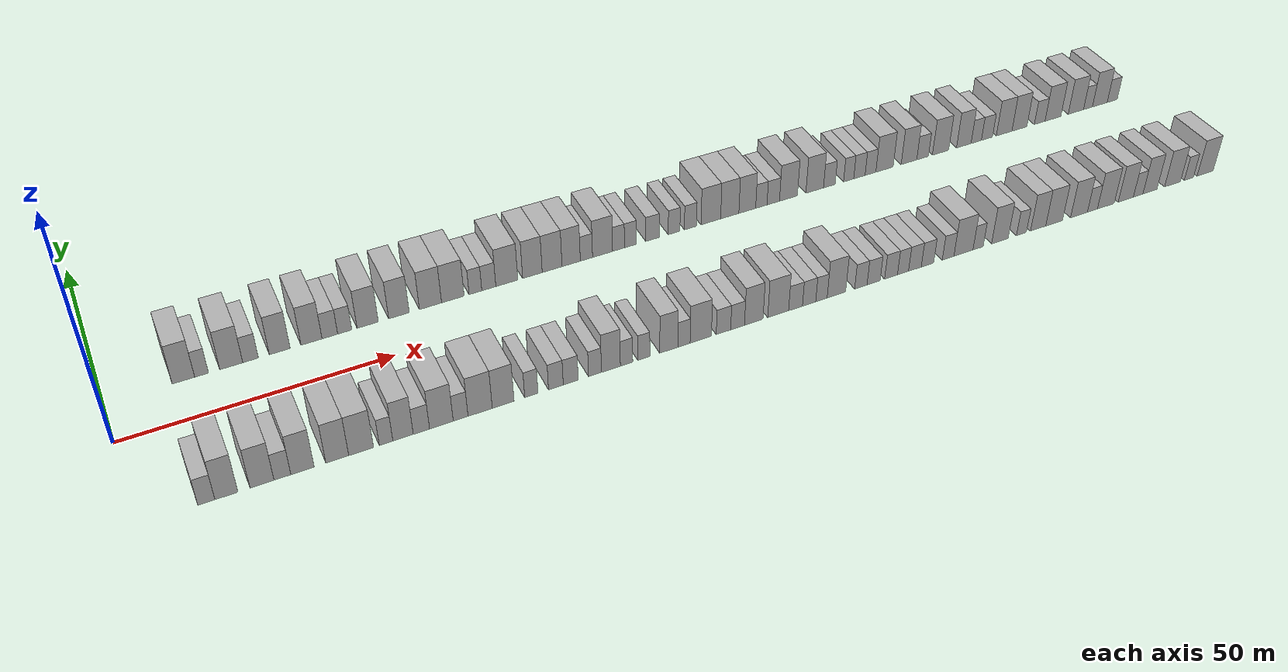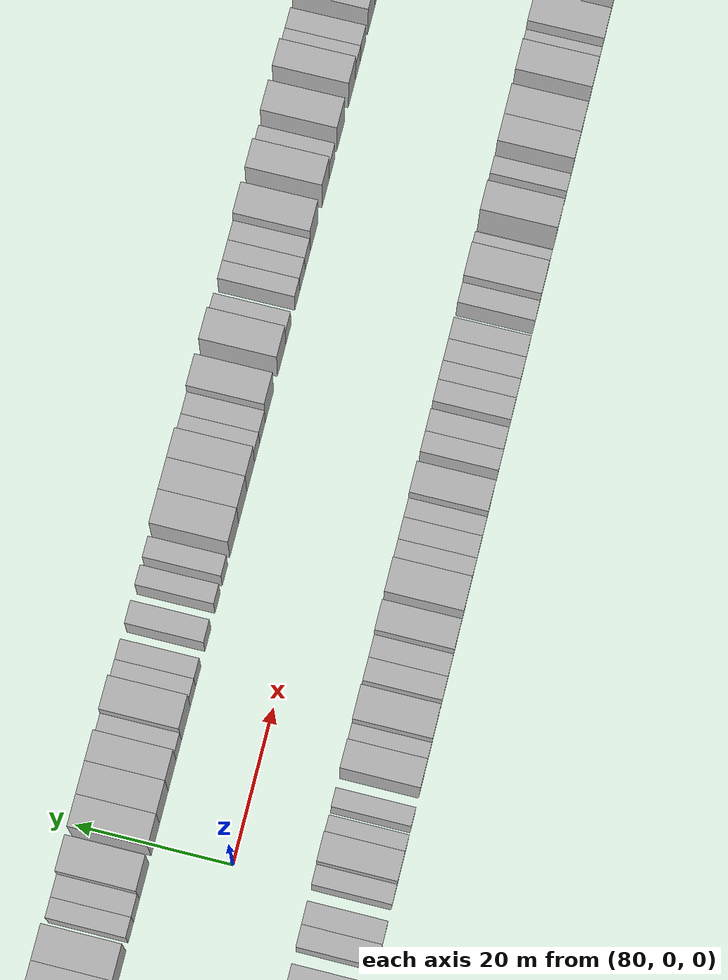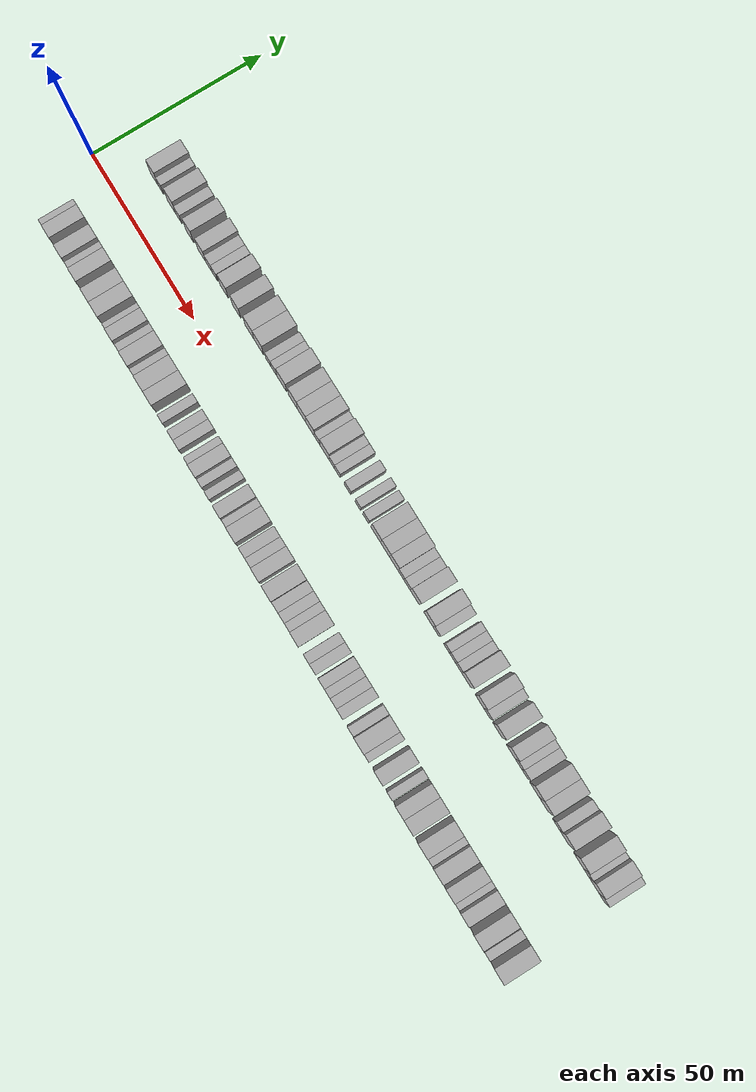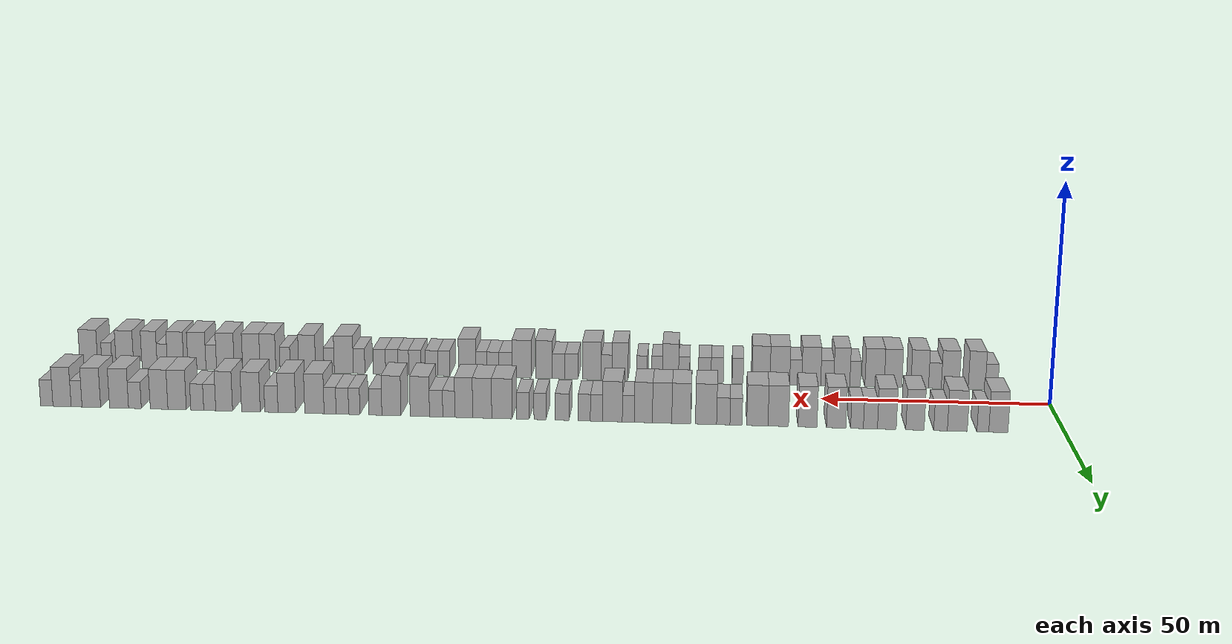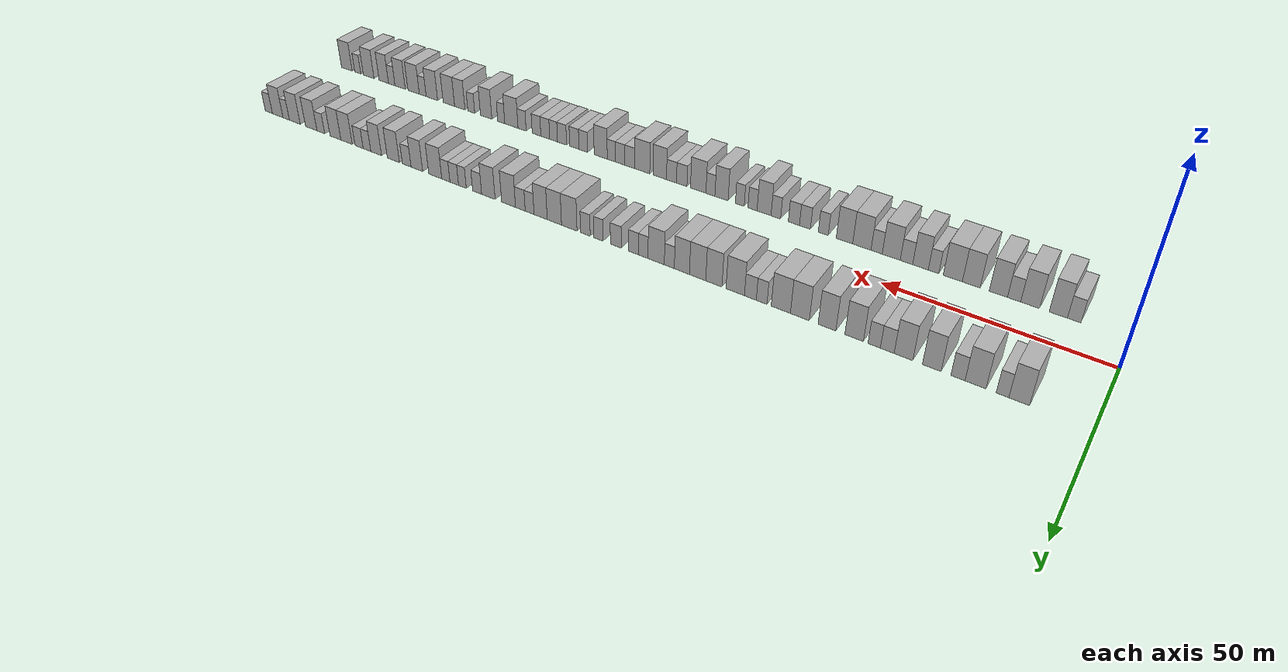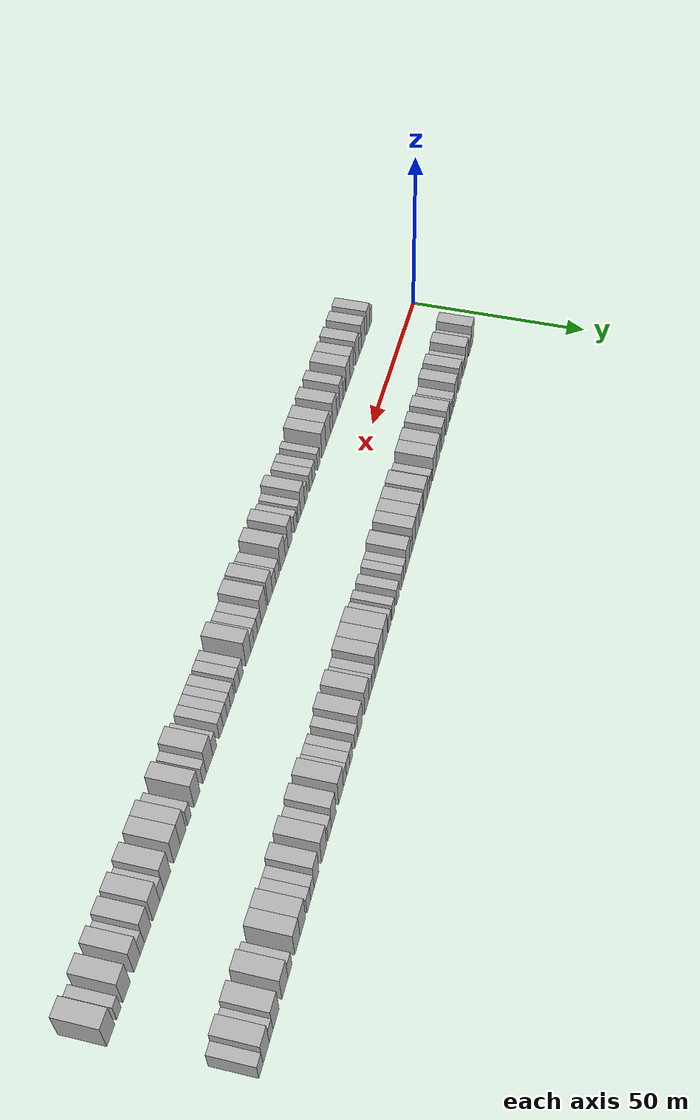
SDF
<sdf version="1.6">
 <world name="default">
  <scene>
   <sky><clouds><speed>12</speed></clouds></sky>
   <ambient>0.4 0.4 0.4 1</ambient>
   <background>0.7 0.7 0.7 1</background>
   <shadows>1</shadows>
  </scene>
  <gravity>0 0 -9.8066</gravity>
  <magnetic_field>6e-06 2.3e-05 -4.2e-05</magnetic_field>
  <physics default="0" name="default_physics" type="ode">
   <ode>
    <solver>
     <type>quick</type>
     <iters>10</iters>
     <sor>1.0</sor>
     <use_dynamic_moi_rescaling>0</use_dynamic_moi_rescaling>
    </solver>
    <constraints>
     <cfm>0</cfm>
     <erp>0.2</erp>
     <contact_max_correcting_vel>100</contact_max_correcting_vel>
     <contact_surface_layer>0.001</contact_surface_layer>
    </constraints>
   </ode>
   <max_step_size>0.004</max_step_size>
   <real_time_factor>1</real_time_factor>
   <real_time_update_rate>250</real_time_update_rate>
  </physics>
  <light name="sun" type="directional">
   <pose>0 0 10 0 0 0</pose>
   <diffuse>0.8 0.8 0.8 1</diffuse>
   <specular>0.2 0.2 0.2 1</specular>
   <attenuation>
    <range>1000</range>
    <constant>0.9</constant>
    <linear>0.01</linear>
    <quadratic>0.001</quadratic>
   </attenuation>
   <direction>-0.5 0.1 -0.9</direction>
  </light>
  <model name="building_1">
   <static>1</static>
   <pose>13.9863 15.0000 0 0.000000 0.000000 1.570796</pose>
   <link name="link">
    <pose>0 0 4.50 0 0 0</pose>
    <collision name="collision"><geometry><box><size>10.0000 3.9726 9.0000</size></box></geometry></collision>
    <visual name="visual">
     <cast_shadows>0</cast_shadows>
     <geometry><box><size>10.0000 3.9726 9.0000</size></box></geometry>
     <material>
      <script>
       <uri>model://HANNAS_wall/materials/scripts</uri>
       <uri>model://HANNAS_wall/materials/textures</uri>
       <name>vrc/HANNAS_wall</name>
      </script>
     </material>
    </visual>
   </link>
  </model>
  <model name="building_2">
   <static>1</static>
   <pose>17.2035 15.0000 0 0.000000 0.000000 1.570796</pose>
   <link name="link">
    <pose>0 0 3.00 0 0 0</pose>
    <collision name="collision"><geometry><box><size>10.0000 2.4617 6.0000</size></box></geometry></collision>
    <visual name="visual">
     <cast_shadows>0</cast_shadows>
     <geometry><box><size>10.0000 2.4617 6.0000</size></box></geometry>
     <material>
      <script>
       <uri>model://HANNAS_wall/materials/scripts</uri>
       <uri>model://HANNAS_wall/materials/textures</uri>
       <name>vrc/HANNAS_wall</name>
      </script>
     </material>
    </visual>
   </link>
  </model>
  <model name="building_3">
   <static>1</static>
   <pose>22.5151 15.0000 0 0.000000 0.000000 1.570796</pose>
   <link name="link">
    <pose>0 0 4.50 0 0 0</pose>
    <collision name="collision"><geometry><box><size>10.0000 4.1615 9.0000</size></box></geometry></collision>
    <visual name="visual">
     <cast_shadows>0</cast_shadows>
     <geometry><box><size>10.0000 4.1615 9.0000</size></box></geometry>
     <material>
      <script>
       <uri>model://HANNAS_wall/materials/scripts</uri>
       <uri>model://HANNAS_wall/materials/textures</uri>
       <name>vrc/HANNAS_wall</name>
      </script>
     </material>
    </visual>
   </link>
  </model>
  <model name="building_4">
   <static>1</static>
   <pose>26.0151 15.0000 0 0.000000 0.000000 1.570796</pose>
   <link name="link">
    <pose>0 0 3.00 0 0 0</pose>
    <collision name="collision"><geometry><box><size>10.0000 2.8385 6.0000</size></box></geometry></collision>
    <visual name="visual">
     <cast_shadows>0</cast_shadows>
     <geometry><box><size>10.0000 2.8385 6.0000</size></box></geometry>
     <material>
      <script>
       <uri>model://HANNAS_wall/materials/scripts</uri>
       <uri>model://HANNAS_wall/materials/textures</uri>
       <name>vrc/HANNAS_wall</name>
      </script>
     </material>
    </visual>
   </link>
  </model>
  <model name="building_5">
   <static>1</static>
   <pose>31.3539 15.0000 0 0.000000 0.000000 1.570796</pose>
   <link name="link">
    <pose>0 0 4.50 0 0 0</pose>
    <collision name="collision"><geometry><box><size>10.0000 3.8392 9.0000</size></box></geometry></collision>
    <visual name="visual">
     <cast_shadows>0</cast_shadows>
     <geometry><box><size>10.0000 3.8392 9.0000</size></box></geometry>
     <material>
      <script>
       <uri>model://HANNAS_wall/materials/scripts</uri>
       <uri>model://HANNAS_wall/materials/textures</uri>
       <name>vrc/HANNAS_wall</name>
      </script>
     </material>
    </visual>
   </link>
  </model>
  <model name="building_6">
   <static>1</static>
   <pose>37.2430 15.0000 0 0.000000 0.000000 1.570796</pose>
   <link name="link">
    <pose>0 0 4.50 0 0 0</pose>
    <collision name="collision"><geometry><box><size>10.0000 3.9389 9.0000</size></box></geometry></collision>
    <visual name="visual">
     <cast_shadows>0</cast_shadows>
     <geometry><box><size>10.0000 3.9389 9.0000</size></box></geometry>
     <material>
      <script>
       <uri>model://HANNAS_wall/materials/scripts</uri>
       <uri>model://HANNAS_wall/materials/textures</uri>
       <name>vrc/HANNAS_wall</name>
      </script>
     </material>
    </visual>
   </link>
  </model>
  <model name="building_7">
   <static>1</static>
   <pose>40.6891 15.0000 0 0.000000 0.000000 1.570796</pose>
   <link name="link">
    <pose>0 0 3.00 0 0 0</pose>
    <collision name="collision"><geometry><box><size>10.0000 2.9532 6.0000</size></box></geometry></collision>
    <visual name="visual">
     <cast_shadows>0</cast_shadows>
     <geometry><box><size>10.0000 2.9532 6.0000</size></box></geometry>
     <material>
      <script>
       <uri>model://HANNAS_wall/materials/scripts</uri>
       <uri>model://HANNAS_wall/materials/textures</uri>
       <name>vrc/HANNAS_wall</name>
      </script>
     </material>
    </visual>
   </link>
  </model>
  <model name="building_8">
   <static>1</static>
   <pose>43.5024 15.0000 0 0.000000 0.000000 1.570796</pose>
   <link name="link">
    <pose>0 0 3.00 0 0 0</pose>
    <collision name="collision"><geometry><box><size>10.0000 2.6734 6.0000</size></box></geometry></collision>
    <visual name="visual">
     <cast_shadows>0</cast_shadows>
     <geometry><box><size>10.0000 2.6734 6.0000</size></box></geometry>
     <material>
      <script>
       <uri>model://HANNAS_wall/materials/scripts</uri>
       <uri>model://HANNAS_wall/materials/textures</uri>
       <name>vrc/HANNAS_wall</name>
      </script>
     </material>
    </visual>
   </link>
  </model>
  <model name="building_9">
   <static>1</static>
   <pose>47.8759 15.0000 0 0.000000 0.000000 1.570796</pose>
   <link name="link">
    <pose>0 0 4.50 0 0 0</pose>
    <collision name="collision"><geometry><box><size>10.0000 4.0736 9.0000</size></box></geometry></collision>
    <visual name="visual">
     <cast_shadows>0</cast_shadows>
     <geometry><box><size>10.0000 4.0736 9.0000</size></box></geometry>
     <material>
      <script>
       <uri>model://HANNAS_wall/materials/scripts</uri>
       <uri>model://HANNAS_wall/materials/textures</uri>
       <name>vrc/HANNAS_wall</name>
      </script>
     </material>
    </visual>
   </link>
  </model>
  <model name="building_10">
   <static>1</static>
   <pose>53.9139 15.0000 0 0.000000 0.000000 1.570796</pose>
   <link name="link">
    <pose>0 0 4.50 0 0 0</pose>
    <collision name="collision"><geometry><box><size>10.0000 4.0025 9.0000</size></box></geometry></collision>
    <visual name="visual">
     <cast_shadows>0</cast_shadows>
     <geometry><box><size>10.0000 4.0025 9.0000</size></box></geometry>
     <material>
      <script>
       <uri>model://HANNAS_wall/materials/scripts</uri>
       <uri>model://HANNAS_wall/materials/textures</uri>
       <name>vrc/HANNAS_wall</name>
      </script>
     </material>
    </visual>
   </link>
  </model>
  <model name="building_11">
   <static>1</static>
   <pose>60.0964 15.0000 0 0.000000 0.000000 1.570796</pose>
   <link name="link">
    <pose>0 0 4.50 0 0 0</pose>
    <collision name="collision"><geometry><box><size>10.0000 4.3625 9.0000</size></box></geometry></collision>
    <visual name="visual">
     <cast_shadows>0</cast_shadows>
     <geometry><box><size>10.0000 4.3625 9.0000</size></box></geometry>
     <material>
      <script>
       <uri>model://HANNAS_wall/materials/scripts</uri>
       <uri>model://HANNAS_wall/materials/textures</uri>
       <name>vrc/HANNAS_wall</name>
      </script>
     </material>
    </visual>
   </link>
  </model>
  <model name="building_12">
   <static>1</static>
   <pose>64.5238 15.0000 0 0.000000 0.000000 1.570796</pose>
   <link name="link">
    <pose>0 0 4.50 0 0 0</pose>
    <collision name="collision"><geometry><box><size>10.0000 4.4922 9.0000</size></box></geometry></collision>
    <visual name="visual">
     <cast_shadows>0</cast_shadows>
     <geometry><box><size>10.0000 4.4922 9.0000</size></box></geometry>
     <material>
      <script>
       <uri>model://HANNAS_wall/materials/scripts</uri>
       <uri>model://HANNAS_wall/materials/textures</uri>
       <name>vrc/HANNAS_wall</name>
      </script>
     </material>
    </visual>
   </link>
  </model>
  <model name="building_13">
   <static>1</static>
   <pose>69.0498 15.0000 0 0.000000 0.000000 1.570796</pose>
   <link name="link">
    <pose>0 0 3.00 0 0 0</pose>
    <collision name="collision"><geometry><box><size>10.0000 2.5598 6.0000</size></box></geometry></collision>
    <visual name="visual">
     <cast_shadows>0</cast_shadows>
     <geometry><box><size>10.0000 2.5598 6.0000</size></box></geometry>
     <material>
      <script>
       <uri>model://HANNAS_wall/materials/scripts</uri>
       <uri>model://HANNAS_wall/materials/textures</uri>
       <name>vrc/HANNAS_wall</name>
      </script>
     </material>
    </visual>
   </link>
  </model>
  <model name="building_14">
   <static>1</static>
   <pose>71.7501 15.0000 0 0.000000 0.000000 1.570796</pose>
   <link name="link">
    <pose>0 0 3.00 0 0 0</pose>
    <collision name="collision"><geometry><box><size>10.0000 2.8408 6.0000</size></box></geometry></collision>
    <visual name="visual">
     <cast_shadows>0</cast_shadows>
     <geometry><box><size>10.0000 2.8408 6.0000</size></box></geometry>
     <material>
      <script>
       <uri>model://HANNAS_wall/materials/scripts</uri>
       <uri>model://HANNAS_wall/materials/textures</uri>
       <name>vrc/HANNAS_wall</name>
      </script>
     </material>
    </visual>
   </link>
  </model>
  <model name="building_15">
   <static>1</static>
   <pose>75.4201 15.0000 0 0.000000 0.000000 1.570796</pose>
   <link name="link">
    <pose>0 0 4.50 0 0 0</pose>
    <collision name="collision"><geometry><box><size>10.0000 4.4993 9.0000</size></box></geometry></collision>
    <visual name="visual">
     <cast_shadows>0</cast_shadows>
     <geometry><box><size>10.0000 4.4993 9.0000</size></box></geometry>
     <material>
      <script>
       <uri>model://HANNAS_wall/materials/scripts</uri>
       <uri>model://HANNAS_wall/materials/textures</uri>
       <name>vrc/HANNAS_wall</name>
      </script>
     </material>
    </visual>
   </link>
  </model>
  <model name="building_16">
   <static>1</static>
   <pose>80.6914 15.0000 0 0.000000 0.000000 1.570796</pose>
   <link name="link">
    <pose>0 0 4.50 0 0 0</pose>
    <collision name="collision"><geometry><box><size>10.0000 4.0434 9.0000</size></box></geometry></collision>
    <visual name="visual">
     <cast_shadows>0</cast_shadows>
     <geometry><box><size>10.0000 4.0434 9.0000</size></box></geometry>
     <material>
      <script>
       <uri>model://HANNAS_wall/materials/scripts</uri>
       <uri>model://HANNAS_wall/materials/textures</uri>
       <name>vrc/HANNAS_wall</name>
      </script>
     </material>
    </visual>
   </link>
  </model>
  <model name="building_17">
   <static>1</static>
   <pose>84.7833 15.0000 0 0.000000 0.000000 1.570796</pose>
   <link name="link">
    <pose>0 0 4.50 0 0 0</pose>
    <collision name="collision"><geometry><box><size>10.0000 4.1405 9.0000</size></box></geometry></collision>
    <visual name="visual">
     <cast_shadows>0</cast_shadows>
     <geometry><box><size>10.0000 4.1405 9.0000</size></box></geometry>
     <material>
      <script>
       <uri>model://HANNAS_wall/materials/scripts</uri>
       <uri>model://HANNAS_wall/materials/textures</uri>
       <name>vrc/HANNAS_wall</name>
      </script>
     </material>
    </visual>
   </link>
  </model>
  <model name="building_18">
   <static>1</static>
   <pose>88.7812 15.0000 0 0.000000 0.000000 1.570796</pose>
   <link name="link">
    <pose>0 0 4.50 0 0 0</pose>
    <collision name="collision"><geometry><box><size>10.0000 3.8553 9.0000</size></box></geometry></collision>
    <visual name="visual">
     <cast_shadows>0</cast_shadows>
     <geometry><box><size>10.0000 3.8553 9.0000</size></box></geometry>
     <material>
      <script>
       <uri>model://HANNAS_wall/materials/scripts</uri>
       <uri>model://HANNAS_wall/materials/textures</uri>
       <name>vrc/HANNAS_wall</name>
      </script>
     </material>
    </visual>
   </link>
  </model>
  <model name="building_19">
   <static>1</static>
   <pose>92.0073 15.0000 0 0.000000 0.000000 1.570796</pose>
   <link name="link">
    <pose>0 0 3.00 0 0 0</pose>
    <collision name="collision"><geometry><box><size>10.0000 2.5967 6.0000</size></box></geometry></collision>
    <visual name="visual">
     <cast_shadows>0</cast_shadows>
     <geometry><box><size>10.0000 2.5967 6.0000</size></box></geometry>
     <material>
      <script>
       <uri>model://HANNAS_wall/materials/scripts</uri>
       <uri>model://HANNAS_wall/materials/textures</uri>
       <name>vrc/HANNAS_wall</name>
      </script>
     </material>
    </visual>
   </link>
  </model>
  <model name="building_20">
   <static>1</static>
   <pose>95.4486 15.0000 0 0.000000 0.000000 1.570796</pose>
   <link name="link">
    <pose>0 0 4.50 0 0 0</pose>
    <collision name="collision"><geometry><box><size>10.0000 4.2859 9.0000</size></box></geometry></collision>
    <visual name="visual">
     <cast_shadows>0</cast_shadows>
     <geometry><box><size>10.0000 4.2859 9.0000</size></box></geometry>
     <material>
      <script>
       <uri>model://HANNAS_wall/materials/scripts</uri>
       <uri>model://HANNAS_wall/materials/textures</uri>
       <name>vrc/HANNAS_wall</name>
      </script>
     </material>
    </visual>
   </link>
  </model>
  <model name="building_21">
   <static>1</static>
   <pose>98.8770 15.0000 0 0.000000 0.000000 1.570796</pose>
   <link name="link">
    <pose>0 0 3.00 0 0 0</pose>
    <collision name="collision"><geometry><box><size>10.0000 2.5709 6.0000</size></box></geometry></collision>
    <visual name="visual">
     <cast_shadows>0</cast_shadows>
     <geometry><box><size>10.0000 2.5709 6.0000</size></box></geometry>
     <material>
      <script>
       <uri>model://HANNAS_wall/materials/scripts</uri>
       <uri>model://HANNAS_wall/materials/textures</uri>
       <name>vrc/HANNAS_wall</name>
      </script>
     </material>
    </visual>
   </link>
  </model>
  <model name="building_22">
   <static>1</static>
   <pose>101.4697 15.0000 0 0.000000 0.000000 1.570796</pose>
   <link name="link">
    <pose>0 0 3.00 0 0 0</pose>
    <collision name="collision"><geometry><box><size>10.0000 2.6144 6.0000</size></box></geometry></collision>
    <visual name="visual">
     <cast_shadows>0</cast_shadows>
     <geometry><box><size>10.0000 2.6144 6.0000</size></box></geometry>
     <material>
      <script>
       <uri>model://HANNAS_wall/materials/scripts</uri>
       <uri>model://HANNAS_wall/materials/textures</uri>
       <name>vrc/HANNAS_wall</name>
      </script>
     </material>
    </visual>
   </link>
  </model>
  <model name="building_23">
   <static>1</static>
   <pose>106.2533 15.0000 0 0.000000 0.000000 1.570796</pose>
   <link name="link">
    <pose>0 0 3.00 0 0 0</pose>
    <collision name="collision"><geometry><box><size>10.0000 2.9528 6.0000</size></box></geometry></collision>
    <visual name="visual">
     <cast_shadows>0</cast_shadows>
     <geometry><box><size>10.0000 2.9528 6.0000</size></box></geometry>
     <material>
      <script>
       <uri>model://HANNAS_wall/materials/scripts</uri>
       <uri>model://HANNAS_wall/materials/textures</uri>
       <name>vrc/HANNAS_wall</name>
      </script>
     </material>
    </visual>
   </link>
  </model>
  <model name="building_24">
   <static>1</static>
   <pose>111.0208 15.0000 0 0.000000 0.000000 1.570796</pose>
   <link name="link">
    <pose>0 0 3.00 0 0 0</pose>
    <collision name="collision"><geometry><box><size>10.0000 2.5822 6.0000</size></box></geometry></collision>
    <visual name="visual">
     <cast_shadows>0</cast_shadows>
     <geometry><box><size>10.0000 2.5822 6.0000</size></box></geometry>
     <material>
      <script>
       <uri>model://HANNAS_wall/materials/scripts</uri>
       <uri>model://HANNAS_wall/materials/textures</uri>
       <name>vrc/HANNAS_wall</name>
      </script>
     </material>
    </visual>
   </link>
  </model>
  <model name="building_25">
   <static>1</static>
   <pose>114.6714 15.0000 0 0.000000 0.000000 1.570796</pose>
   <link name="link">
    <pose>0 0 3.00 0 0 0</pose>
    <collision name="collision"><geometry><box><size>10.0000 2.7189 6.0000</size></box></geometry></collision>
    <visual name="visual">
     <cast_shadows>0</cast_shadows>
     <geometry><box><size>10.0000 2.7189 6.0000</size></box></geometry>
     <material>
      <script>
       <uri>model://HANNAS_wall/materials/scripts</uri>
       <uri>model://HANNAS_wall/materials/textures</uri>
       <name>vrc/HANNAS_wall</name>
      </script>
     </material>
    </visual>
   </link>
  </model>
  <model name="building_26">
   <static>1</static>
   <pose>119.2425 15.0000 0 0.000000 0.000000 1.570796</pose>
   <link name="link">
    <pose>0 0 4.50 0 0 0</pose>
    <collision name="collision"><geometry><box><size>10.0000 4.4233 9.0000</size></box></geometry></collision>
    <visual name="visual">
     <cast_shadows>0</cast_shadows>
     <geometry><box><size>10.0000 4.4233 9.0000</size></box></geometry>
     <material>
      <script>
       <uri>model://HANNAS_wall/materials/scripts</uri>
       <uri>model://HANNAS_wall/materials/textures</uri>
       <name>vrc/HANNAS_wall</name>
      </script>
     </material>
    </visual>
   </link>
  </model>
  <model name="building_27">
   <static>1</static>
   <pose>123.5292 15.0000 0 0.000000 0.000000 1.570796</pose>
   <link name="link">
    <pose>0 0 4.50 0 0 0</pose>
    <collision name="collision"><geometry><box><size>10.0000 4.1503 9.0000</size></box></geometry></collision>
    <visual name="visual">
     <cast_shadows>0</cast_shadows>
     <geometry><box><size>10.0000 4.1503 9.0000</size></box></geometry>
     <material>
      <script>
       <uri>model://HANNAS_wall/materials/scripts</uri>
       <uri>model://HANNAS_wall/materials/textures</uri>
       <name>vrc/HANNAS_wall</name>
      </script>
     </material>
    </visual>
   </link>
  </model>
  <model name="building_28">
   <static>1</static>
   <pose>127.5365 15.0000 0 0.000000 0.000000 1.570796</pose>
   <link name="link">
    <pose>0 0 4.50 0 0 0</pose>
    <collision name="collision"><geometry><box><size>10.0000 3.8643 9.0000</size></box></geometry></collision>
    <visual name="visual">
     <cast_shadows>0</cast_shadows>
     <geometry><box><size>10.0000 3.8643 9.0000</size></box></geometry>
     <material>
      <script>
       <uri>model://HANNAS_wall/materials/scripts</uri>
       <uri>model://HANNAS_wall/materials/textures</uri>
       <name>vrc/HANNAS_wall</name>
      </script>
     </material>
    </visual>
   </link>
  </model>
  <model name="building_29">
   <static>1</static>
   <pose>130.7800 15.0000 0 0.000000 0.000000 1.570796</pose>
   <link name="link">
    <pose>0 0 3.00 0 0 0</pose>
    <collision name="collision"><geometry><box><size>10.0000 2.6229 6.0000</size></box></geometry></collision>
    <visual name="visual">
     <cast_shadows>0</cast_shadows>
     <geometry><box><size>10.0000 2.6229 6.0000</size></box></geometry>
     <material>
      <script>
       <uri>model://HANNAS_wall/materials/scripts</uri>
       <uri>model://HANNAS_wall/materials/textures</uri>
       <name>vrc/HANNAS_wall</name>
      </script>
     </material>
    </visual>
   </link>
  </model>
  <model name="building_30">
   <static>1</static>
   <pose>133.5405 15.0000 0 0.000000 0.000000 1.570796</pose>
   <link name="link">
    <pose>0 0 3.00 0 0 0</pose>
    <collision name="collision"><geometry><box><size>10.0000 2.8981 6.0000</size></box></geometry></collision>
    <visual name="visual">
     <cast_shadows>0</cast_shadows>
     <geometry><box><size>10.0000 2.8981 6.0000</size></box></geometry>
     <material>
      <script>
       <uri>model://HANNAS_wall/materials/scripts</uri>
       <uri>model://HANNAS_wall/materials/textures</uri>
       <name>vrc/HANNAS_wall</name>
      </script>
     </material>
    </visual>
   </link>
  </model>
  <model name="building_31">
   <static>1</static>
   <pose>137.0973 15.0000 0 0.000000 0.000000 1.570796</pose>
   <link name="link">
    <pose>0 0 4.50 0 0 0</pose>
    <collision name="collision"><geometry><box><size>10.0000 4.2155 9.0000</size></box></geometry></collision>
    <visual name="visual">
     <cast_shadows>0</cast_shadows>
     <geometry><box><size>10.0000 4.2155 9.0000</size></box></geometry>
     <material>
      <script>
       <uri>model://HANNAS_wall/materials/scripts</uri>
       <uri>model://HANNAS_wall/materials/textures</uri>
       <name>vrc/HANNAS_wall</name>
      </script>
     </material>
    </visual>
   </link>
  </model>
  <model name="building_32">
   <static>1</static>
   <pose>143.2945 15.0000 0 0.000000 0.000000 1.570796</pose>
   <link name="link">
    <pose>0 0 4.50 0 0 0</pose>
    <collision name="collision"><geometry><box><size>10.0000 4.1790 9.0000</size></box></geometry></collision>
    <visual name="visual">
     <cast_shadows>0</cast_shadows>
     <geometry><box><size>10.0000 4.1790 9.0000</size></box></geometry>
     <material>
      <script>
       <uri>model://HANNAS_wall/materials/scripts</uri>
       <uri>model://HANNAS_wall/materials/textures</uri>
       <name>vrc/HANNAS_wall</name>
      </script>
     </material>
    </visual>
   </link>
  </model>
  <model name="building_33">
   <static>1</static>
   <pose>146.7900 15.0000 0 0.000000 0.000000 1.570796</pose>
   <link name="link">
    <pose>0 0 3.00 0 0 0</pose>
    <collision name="collision"><geometry><box><size>10.0000 2.8119 6.0000</size></box></geometry></collision>
    <visual name="visual">
     <cast_shadows>0</cast_shadows>
     <geometry><box><size>10.0000 2.8119 6.0000</size></box></geometry>
     <material>
      <script>
       <uri>model://HANNAS_wall/materials/scripts</uri>
       <uri>model://HANNAS_wall/materials/textures</uri>
       <name>vrc/HANNAS_wall</name>
      </script>
     </material>
    </visual>
   </link>
  </model>
  <model name="building_34">
   <static>1</static>
   <pose>151.4294 15.0000 0 0.000000 0.000000 1.570796</pose>
   <link name="link">
    <pose>0 0 3.00 0 0 0</pose>
    <collision name="collision"><geometry><box><size>10.0000 2.4668 6.0000</size></box></geometry></collision>
    <visual name="visual">
     <cast_shadows>0</cast_shadows>
     <geometry><box><size>10.0000 2.4668 6.0000</size></box></geometry>
     <material>
      <script>
       <uri>model://HANNAS_wall/materials/scripts</uri>
       <uri>model://HANNAS_wall/materials/textures</uri>
       <name>vrc/HANNAS_wall</name>
      </script>
     </material>
    </visual>
   </link>
  </model>
  <model name="building_35">
   <static>1</static>
   <pose>154.0448 15.0000 0 0.000000 0.000000 1.570796</pose>
   <link name="link">
    <pose>0 0 3.00 0 0 0</pose>
    <collision name="collision"><geometry><box><size>10.0000 2.7641 6.0000</size></box></geometry></collision>
    <visual name="visual">
     <cast_shadows>0</cast_shadows>
     <geometry><box><size>10.0000 2.7641 6.0000</size></box></geometry>
     <material>
      <script>
       <uri>model://HANNAS_wall/materials/scripts</uri>
       <uri>model://HANNAS_wall/materials/textures</uri>
       <name>vrc/HANNAS_wall</name>
      </script>
     </material>
    </visual>
   </link>
  </model>
  <model name="building_36">
   <static>1</static>
   <pose>156.7458 15.0000 0 0.000000 0.000000 1.570796</pose>
   <link name="link">
    <pose>0 0 3.00 0 0 0</pose>
    <collision name="collision"><geometry><box><size>10.0000 2.6380 6.0000</size></box></geometry></collision>
    <visual name="visual">
     <cast_shadows>0</cast_shadows>
     <geometry><box><size>10.0000 2.6380 6.0000</size></box></geometry>
     <material>
      <script>
       <uri>model://HANNAS_wall/materials/scripts</uri>
       <uri>model://HANNAS_wall/materials/textures</uri>
       <name>vrc/HANNAS_wall</name>
      </script>
     </material>
    </visual>
   </link>
  </model>
  <model name="building_37">
   <static>1</static>
   <pose>160.1915 15.0000 0 0.000000 0.000000 1.570796</pose>
   <link name="link">
    <pose>0 0 4.50 0 0 0</pose>
    <collision name="collision"><geometry><box><size>10.0000 4.2535 9.0000</size></box></geometry></collision>
    <visual name="visual">
     <cast_shadows>0</cast_shadows>
     <geometry><box><size>10.0000 4.2535 9.0000</size></box></geometry>
     <material>
      <script>
       <uri>model://HANNAS_wall/materials/scripts</uri>
       <uri>model://HANNAS_wall/materials/textures</uri>
       <name>vrc/HANNAS_wall</name>
      </script>
     </material>
    </visual>
   </link>
  </model>
  <model name="building_38">
   <static>1</static>
   <pose>166.2654 15.0000 0 0.000000 0.000000 1.570796</pose>
   <link name="link">
    <pose>0 0 4.50 0 0 0</pose>
    <collision name="collision"><geometry><box><size>10.0000 3.8942 9.0000</size></box></geometry></collision>
    <visual name="visual">
     <cast_shadows>0</cast_shadows>
     <geometry><box><size>10.0000 3.8942 9.0000</size></box></geometry>
     <material>
      <script>
       <uri>model://HANNAS_wall/materials/scripts</uri>
       <uri>model://HANNAS_wall/materials/textures</uri>
       <name>vrc/HANNAS_wall</name>
      </script>
     </material>
    </visual>
   </link>
  </model>
  <model name="building_39">
   <static>1</static>
   <pose>169.6782 15.0000 0 0.000000 0.000000 1.570796</pose>
   <link name="link">
    <pose>0 0 3.00 0 0 0</pose>
    <collision name="collision"><geometry><box><size>10.0000 2.9316 6.0000</size></box></geometry></collision>
    <visual name="visual">
     <cast_shadows>0</cast_shadows>
     <geometry><box><size>10.0000 2.9316 6.0000</size></box></geometry>
     <material>
      <script>
       <uri>model://HANNAS_wall/materials/scripts</uri>
       <uri>model://HANNAS_wall/materials/textures</uri>
       <name>vrc/HANNAS_wall</name>
      </script>
     </material>
    </visual>
   </link>
  </model>
  <model name="building_40">
   <static>1</static>
   <pose>174.2125 15.0000 0 0.000000 0.000000 1.570796</pose>
   <link name="link">
    <pose>0 0 4.50 0 0 0</pose>
    <collision name="collision"><geometry><box><size>10.0000 4.1370 9.0000</size></box></geometry></collision>
    <visual name="visual">
     <cast_shadows>0</cast_shadows>
     <geometry><box><size>10.0000 4.1370 9.0000</size></box></geometry>
     <material>
      <script>
       <uri>model://HANNAS_wall/materials/scripts</uri>
       <uri>model://HANNAS_wall/materials/textures</uri>
       <name>vrc/HANNAS_wall</name>
      </script>
     </material>
    </visual>
   </link>
  </model>
  <model name="building_41">
   <static>1</static>
   <pose>180.1501 15.0000 0 0.000000 0.000000 1.570796</pose>
   <link name="link">
    <pose>0 0 4.50 0 0 0</pose>
    <collision name="collision"><geometry><box><size>10.0000 3.7381 9.0000</size></box></geometry></collision>
    <visual name="visual">
     <cast_shadows>0</cast_shadows>
     <geometry><box><size>10.0000 3.7381 9.0000</size></box></geometry>
     <material>
      <script>
       <uri>model://HANNAS_wall/materials/scripts</uri>
       <uri>model://HANNAS_wall/materials/textures</uri>
       <name>vrc/HANNAS_wall</name>
      </script>
     </material>
    </visual>
   </link>
  </model>
  <model name="building_42">
   <static>1</static>
   <pose>183.3578 15.0000 0 0.000000 0.000000 1.570796</pose>
   <link name="link">
    <pose>0 0 3.00 0 0 0</pose>
    <collision name="collision"><geometry><box><size>10.0000 2.6774 6.0000</size></box></geometry></collision>
    <visual name="visual">
     <cast_shadows>0</cast_shadows>
     <geometry><box><size>10.0000 2.6774 6.0000</size></box></geometry>
     <material>
      <script>
       <uri>model://HANNAS_wall/materials/scripts</uri>
       <uri>model://HANNAS_wall/materials/textures</uri>
       <name>vrc/HANNAS_wall</name>
      </script>
     </material>
    </visual>
   </link>
  </model>
  <model name="building_43">
   <static>1</static>
   <pose>186.1347 15.0000 0 0.000000 0.000000 1.570796</pose>
   <link name="link">
    <pose>0 0 3.00 0 0 0</pose>
    <collision name="collision"><geometry><box><size>10.0000 2.8764 6.0000</size></box></geometry></collision>
    <visual name="visual">
     <cast_shadows>0</cast_shadows>
     <geometry><box><size>10.0000 2.8764 6.0000</size></box></geometry>
     <material>
      <script>
       <uri>model://HANNAS_wall/materials/scripts</uri>
       <uri>model://HANNAS_wall/materials/textures</uri>
       <name>vrc/HANNAS_wall</name>
      </script>
     </material>
    </visual>
   </link>
  </model>
  <model name="building_44">
   <static>1</static>
   <pose>190.6257 15.0000 0 0.000000 0.000000 1.570796</pose>
   <link name="link">
    <pose>0 0 4.50 0 0 0</pose>
    <collision name="collision"><geometry><box><size>10.0000 4.1056 9.0000</size></box></geometry></collision>
    <visual name="visual">
     <cast_shadows>0</cast_shadows>
     <geometry><box><size>10.0000 4.1056 9.0000</size></box></geometry>
     <material>
      <script>
       <uri>model://HANNAS_wall/materials/scripts</uri>
       <uri>model://HANNAS_wall/materials/textures</uri>
       <name>vrc/HANNAS_wall</name>
      </script>
     </material>
    </visual>
   </link>
  </model>
  <model name="building_45">
   <static>1</static>
   <pose>194.6477 15.0000 0 0.000000 0.000000 1.570796</pose>
   <link name="link">
    <pose>0 0 4.50 0 0 0</pose>
    <collision name="collision"><geometry><box><size>10.0000 3.9384 9.0000</size></box></geometry></collision>
    <visual name="visual">
     <cast_shadows>0</cast_shadows>
     <geometry><box><size>10.0000 3.9384 9.0000</size></box></geometry>
     <material>
      <script>
       <uri>model://HANNAS_wall/materials/scripts</uri>
       <uri>model://HANNAS_wall/materials/textures</uri>
       <name>vrc/HANNAS_wall</name>
      </script>
     </material>
    </visual>
   </link>
  </model>
  <model name="building_46">
   <static>1</static>
   <pose>200.0471 15.0000 0 0.000000 0.000000 1.570796</pose>
   <link name="link">
    <pose>0 0 3.00 0 0 0</pose>
    <collision name="collision"><geometry><box><size>10.0000 2.8604 6.0000</size></box></geometry></collision>
    <visual name="visual">
     <cast_shadows>0</cast_shadows>
     <geometry><box><size>10.0000 2.8604 6.0000</size></box></geometry>
     <material>
      <script>
       <uri>model://HANNAS_wall/materials/scripts</uri>
       <uri>model://HANNAS_wall/materials/textures</uri>
       <name>vrc/HANNAS_wall</name>
      </script>
     </material>
    </visual>
   </link>
  </model>
  <model name="building_47">
   <static>1</static>
   <pose>203.6051 15.0000 0 0.000000 0.000000 1.570796</pose>
   <link name="link">
    <pose>0 0 4.50 0 0 0</pose>
    <collision name="collision"><geometry><box><size>10.0000 4.2556 9.0000</size></box></geometry></collision>
    <visual name="visual">
     <cast_shadows>0</cast_shadows>
     <geometry><box><size>10.0000 4.2556 9.0000</size></box></geometry>
     <material>
      <script>
       <uri>model://HANNAS_wall/materials/scripts</uri>
       <uri>model://HANNAS_wall/materials/textures</uri>
       <name>vrc/HANNAS_wall</name>
      </script>
     </material>
    </visual>
   </link>
  </model>
  <model name="building_48">
   <static>1</static>
   <pose>209.8230 15.0000 0 0.000000 0.000000 1.570796</pose>
   <link name="link">
    <pose>0 0 4.50 0 0 0</pose>
    <collision name="collision"><geometry><box><size>10.0000 4.1801 9.0000</size></box></geometry></collision>
    <visual name="visual">
     <cast_shadows>0</cast_shadows>
     <geometry><box><size>10.0000 4.1801 9.0000</size></box></geometry>
     <material>
      <script>
       <uri>model://HANNAS_wall/materials/scripts</uri>
       <uri>model://HANNAS_wall/materials/textures</uri>
       <name>vrc/HANNAS_wall</name>
      </script>
     </material>
    </visual>
   </link>
  </model>
  <model name="building_49">
   <static>1</static>
   <pose>213.1358 15.0000 0 0.000000 0.000000 1.570796</pose>
   <link name="link">
    <pose>0 0 3.00 0 0 0</pose>
    <collision name="collision"><geometry><box><size>10.0000 2.4456 6.0000</size></box></geometry></collision>
    <visual name="visual">
     <cast_shadows>0</cast_shadows>
     <geometry><box><size>10.0000 2.4456 6.0000</size></box></geometry>
     <material>
      <script>
       <uri>model://HANNAS_wall/materials/scripts</uri>
       <uri>model://HANNAS_wall/materials/textures</uri>
       <name>vrc/HANNAS_wall</name>
      </script>
     </material>
    </visual>
   </link>
  </model>
  <model name="building_50">
   <static>1</static>
   <pose>216.4056 15.0000 0 0.000000 0.000000 1.570796</pose>
   <link name="link">
    <pose>0 0 4.50 0 0 0</pose>
    <collision name="collision"><geometry><box><size>10.0000 4.0941 9.0000</size></box></geometry></collision>
    <visual name="visual">
     <cast_shadows>0</cast_shadows>
     <geometry><box><size>10.0000 4.0941 9.0000</size></box></geometry>
     <material>
      <script>
       <uri>model://HANNAS_wall/materials/scripts</uri>
       <uri>model://HANNAS_wall/materials/textures</uri>
       <name>vrc/HANNAS_wall</name>
      </script>
     </material>
    </visual>
   </link>
  </model>
  <model name="building_51">
   <static>1</static>
   <pose>219.8437 15.0000 0 0.000000 0.000000 1.570796</pose>
   <link name="link">
    <pose>0 0 3.00 0 0 0</pose>
    <collision name="collision"><geometry><box><size>10.0000 2.7820 6.0000</size></box></geometry></collision>
    <visual name="visual">
     <cast_shadows>0</cast_shadows>
     <geometry><box><size>10.0000 2.7820 6.0000</size></box></geometry>
     <material>
      <script>
       <uri>model://HANNAS_wall/materials/scripts</uri>
       <uri>model://HANNAS_wall/materials/textures</uri>
       <name>vrc/HANNAS_wall</name>
      </script>
     </material>
    </visual>
   </link>
  </model>
  <model name="building_52">
   <static>1</static>
   <pose>11.3973 -15.0000 0 0.000000 0.000000 1.570796</pose>
   <link name="link">
    <pose>0 0 3.00 0 0 0</pose>
    <collision name="collision"><geometry><box><size>10.0000 2.7946 6.0000</size></box></geometry></collision>
    <visual name="visual">
     <cast_shadows>0</cast_shadows>
     <geometry><box><size>10.0000 2.7946 6.0000</size></box></geometry>
     <material>
      <script>
       <uri>model://HANNAS_wall/materials/scripts</uri>
       <uri>model://HANNAS_wall/materials/textures</uri>
       <name>vrc/HANNAS_wall</name>
      </script>
     </material>
    </visual>
   </link>
  </model>
  <model name="building_53">
   <static>1</static>
   <pose>14.6870 -15.0000 0 0.000000 0.000000 1.570796</pose>
   <link name="link">
    <pose>0 0 4.50 0 0 0</pose>
    <collision name="collision"><geometry><box><size>10.0000 3.7847 9.0000</size></box></geometry></collision>
    <visual name="visual">
     <cast_shadows>0</cast_shadows>
     <geometry><box><size>10.0000 3.7847 9.0000</size></box></geometry>
     <material>
      <script>
       <uri>model://HANNAS_wall/materials/scripts</uri>
       <uri>model://HANNAS_wall/materials/textures</uri>
       <name>vrc/HANNAS_wall</name>
      </script>
     </material>
    </visual>
   </link>
  </model>
  <model name="building_54">
   <static>1</static>
   <pose>20.5842 -15.0000 0 0.000000 0.000000 1.570796</pose>
   <link name="link">
    <pose>0 0 4.50 0 0 0</pose>
    <collision name="collision"><geometry><box><size>10.0000 4.0096 9.0000</size></box></geometry></collision>
    <visual name="visual">
     <cast_shadows>0</cast_shadows>
     <geometry><box><size>10.0000 4.0096 9.0000</size></box></geometry>
     <material>
      <script>
       <uri>model://HANNAS_wall/materials/scripts</uri>
       <uri>model://HANNAS_wall/materials/textures</uri>
       <name>vrc/HANNAS_wall</name>
      </script>
     </material>
    </visual>
   </link>
  </model>
  <model name="building_55">
   <static>1</static>
   <pose>24.0114 -15.0000 0 0.000000 0.000000 1.570796</pose>
   <link name="link">
    <pose>0 0 3.00 0 0 0</pose>
    <collision name="collision"><geometry><box><size>10.0000 2.8448 6.0000</size></box></geometry></collision>
    <visual name="visual">
     <cast_shadows>0</cast_shadows>
     <geometry><box><size>10.0000 2.8448 6.0000</size></box></geometry>
     <material>
      <script>
       <uri>model://HANNAS_wall/materials/scripts</uri>
       <uri>model://HANNAS_wall/materials/textures</uri>
       <name>vrc/HANNAS_wall</name>
      </script>
     </material>
    </visual>
   </link>
  </model>
  <model name="building_56">
   <static>1</static>
   <pose>27.4137 -15.0000 0 0.000000 0.000000 1.570796</pose>
   <link name="link">
    <pose>0 0 4.50 0 0 0</pose>
    <collision name="collision"><geometry><box><size>10.0000 3.9599 9.0000</size></box></geometry></collision>
    <visual name="visual">
     <cast_shadows>0</cast_shadows>
     <geometry><box><size>10.0000 3.9599 9.0000</size></box></geometry>
     <material>
      <script>
       <uri>model://HANNAS_wall/materials/scripts</uri>
       <uri>model://HANNAS_wall/materials/textures</uri>
       <name>vrc/HANNAS_wall</name>
      </script>
     </material>
    </visual>
   </link>
  </model>
  <model name="building_57">
   <static>1</static>
   <pose>33.3716 -15.0000 0 0.000000 0.000000 1.570796</pose>
   <link name="link">
    <pose>0 0 4.50 0 0 0</pose>
    <collision name="collision"><geometry><box><size>10.0000 3.9559 9.0000</size></box></geometry></collision>
    <visual name="visual">
     <cast_shadows>0</cast_shadows>
     <geometry><box><size>10.0000 3.9559 9.0000</size></box></geometry>
     <material>
      <script>
       <uri>model://HANNAS_wall/materials/scripts</uri>
       <uri>model://HANNAS_wall/materials/textures</uri>
       <name>vrc/HANNAS_wall</name>
      </script>
     </material>
    </visual>
   </link>
  </model>
  <model name="building_58">
   <static>1</static>
   <pose>37.5189 -15.0000 0 0.000000 0.000000 1.570796</pose>
   <link name="link">
    <pose>0 0 4.50 0 0 0</pose>
    <collision name="collision"><geometry><box><size>10.0000 4.3388 9.0000</size></box></geometry></collision>
    <visual name="visual">
     <cast_shadows>0</cast_shadows>
     <geometry><box><size>10.0000 4.3388 9.0000</size></box></geometry>
     <material>
      <script>
       <uri>model://HANNAS_wall/materials/scripts</uri>
       <uri>model://HANNAS_wall/materials/textures</uri>
       <name>vrc/HANNAS_wall</name>
      </script>
     </material>
    </visual>
   </link>
  </model>
  <model name="building_59">
   <static>1</static>
   <pose>41.8885 -15.0000 0 0.000000 0.000000 1.570796</pose>
   <link name="link">
    <pose>0 0 3.00 0 0 0</pose>
    <collision name="collision"><geometry><box><size>10.0000 2.4004 6.0000</size></box></geometry></collision>
    <visual name="visual">
     <cast_shadows>0</cast_shadows>
     <geometry><box><size>10.0000 2.4004 6.0000</size></box></geometry>
     <material>
      <script>
       <uri>model://HANNAS_wall/materials/scripts</uri>
       <uri>model://HANNAS_wall/materials/textures</uri>
       <name>vrc/HANNAS_wall</name>
      </script>
     </material>
    </visual>
   </link>
  </model>
  <model name="building_60">
   <static>1</static>
   <pose>44.9065 -15.0000 0 0.000000 0.000000 1.570796</pose>
   <link name="link">
    <pose>0 0 4.50 0 0 0</pose>
    <collision name="collision"><geometry><box><size>10.0000 3.6356 9.0000</size></box></geometry></collision>
    <visual name="visual">
     <cast_shadows>0</cast_shadows>
     <geometry><box><size>10.0000 3.6356 9.0000</size></box></geometry>
     <material>
      <script>
       <uri>model://HANNAS_wall/materials/scripts</uri>
       <uri>model://HANNAS_wall/materials/textures</uri>
       <name>vrc/HANNAS_wall</name>
      </script>
     </material>
    </visual>
   </link>
  </model>
  <model name="building_61">
   <static>1</static>
   <pose>48.1842 -15.0000 0 0.000000 0.000000 1.570796</pose>
   <link name="link">
    <pose>0 0 3.00 0 0 0</pose>
    <collision name="collision"><geometry><box><size>10.0000 2.9200 6.0000</size></box></geometry></collision>
    <visual name="visual">
     <cast_shadows>0</cast_shadows>
     <geometry><box><size>10.0000 2.9200 6.0000</size></box></geometry>
     <material>
      <script>
       <uri>model://HANNAS_wall/materials/scripts</uri>
       <uri>model://HANNAS_wall/materials/textures</uri>
       <name>vrc/HANNAS_wall</name>
      </script>
     </material>
    </visual>
   </link>
  </model>
  <model name="building_62">
   <static>1</static>
   <pose>51.7884 -15.0000 0 0.000000 0.000000 1.570796</pose>
   <link name="link">
    <pose>0 0 4.50 0 0 0</pose>
    <collision name="collision"><geometry><box><size>10.0000 4.2884 9.0000</size></box></geometry></collision>
    <visual name="visual">
     <cast_shadows>0</cast_shadows>
     <geometry><box><size>10.0000 4.2884 9.0000</size></box></geometry>
     <material>
      <script>
       <uri>model://HANNAS_wall/materials/scripts</uri>
       <uri>model://HANNAS_wall/materials/textures</uri>
       <name>vrc/HANNAS_wall</name>
      </script>
     </material>
    </visual>
   </link>
  </model>
  <model name="building_63">
   <static>1</static>
   <pose>55.2880 -15.0000 0 0.000000 0.000000 1.570796</pose>
   <link name="link">
    <pose>0 0 3.00 0 0 0</pose>
    <collision name="collision"><geometry><box><size>10.0000 2.7107 6.0000</size></box></geometry></collision>
    <visual name="visual">
     <cast_shadows>0</cast_shadows>
     <geometry><box><size>10.0000 2.7107 6.0000</size></box></geometry>
     <material>
      <script>
       <uri>model://HANNAS_wall/materials/scripts</uri>
       <uri>model://HANNAS_wall/materials/textures</uri>
       <name>vrc/HANNAS_wall</name>
      </script>
     </material>
    </visual>
   </link>
  </model>
  <model name="building_64">
   <static>1</static>
   <pose>58.8782 -15.0000 0 0.000000 0.000000 1.570796</pose>
   <link name="link">
    <pose>0 0 4.50 0 0 0</pose>
    <collision name="collision"><geometry><box><size>10.0000 4.4697 9.0000</size></box></geometry></collision>
    <visual name="visual">
     <cast_shadows>0</cast_shadows>
     <geometry><box><size>10.0000 4.4697 9.0000</size></box></geometry>
     <material>
      <script>
       <uri>model://HANNAS_wall/materials/scripts</uri>
       <uri>model://HANNAS_wall/materials/textures</uri>
       <name>vrc/HANNAS_wall</name>
      </script>
     </material>
    </visual>
   </link>
  </model>
  <model name="building_65">
   <static>1</static>
   <pose>63.1442 -15.0000 0 0.000000 0.000000 1.570796</pose>
   <link name="link">
    <pose>0 0 4.50 0 0 0</pose>
    <collision name="collision"><geometry><box><size>10.0000 4.0622 9.0000</size></box></geometry></collision>
    <visual name="visual">
     <cast_shadows>0</cast_shadows>
     <geometry><box><size>10.0000 4.0622 9.0000</size></box></geometry>
     <material>
      <script>
       <uri>model://HANNAS_wall/materials/scripts</uri>
       <uri>model://HANNAS_wall/materials/textures</uri>
       <name>vrc/HANNAS_wall</name>
      </script>
     </material>
    </visual>
   </link>
  </model>
  <model name="building_66">
   <static>1</static>
   <pose>68.4313 -15.0000 0 0.000000 0.000000 1.570796</pose>
   <link name="link">
    <pose>0 0 3.00 0 0 0</pose>
    <collision name="collision"><geometry><box><size>10.0000 2.5121 6.0000</size></box></geometry></collision>
    <visual name="visual">
     <cast_shadows>0</cast_shadows>
     <geometry><box><size>10.0000 2.5121 6.0000</size></box></geometry>
     <material>
      <script>
       <uri>model://HANNAS_wall/materials/scripts</uri>
       <uri>model://HANNAS_wall/materials/textures</uri>
       <name>vrc/HANNAS_wall</name>
      </script>
     </material>
    </visual>
   </link>
  </model>
  <model name="building_67">
   <static>1</static>
   <pose>73.0961 -15.0000 0 0.000000 0.000000 1.570796</pose>
   <link name="link">
    <pose>0 0 3.00 0 0 0</pose>
    <collision name="collision"><geometry><box><size>10.0000 2.8175 6.0000</size></box></geometry></collision>
    <visual name="visual">
     <cast_shadows>0</cast_shadows>
     <geometry><box><size>10.0000 2.8175 6.0000</size></box></geometry>
     <material>
      <script>
       <uri>model://HANNAS_wall/materials/scripts</uri>
       <uri>model://HANNAS_wall/materials/textures</uri>
       <name>vrc/HANNAS_wall</name>
      </script>
     </material>
    </visual>
   </link>
  </model>
  <model name="building_68">
   <static>1</static>
   <pose>75.9450 -15.0000 0 0.000000 0.000000 1.570796</pose>
   <link name="link">
    <pose>0 0 3.00 0 0 0</pose>
    <collision name="collision"><geometry><box><size>10.0000 2.8802 6.0000</size></box></geometry></collision>
    <visual name="visual">
     <cast_shadows>0</cast_shadows>
     <geometry><box><size>10.0000 2.8802 6.0000</size></box></geometry>
     <material>
      <script>
       <uri>model://HANNAS_wall/materials/scripts</uri>
       <uri>model://HANNAS_wall/materials/textures</uri>
       <name>vrc/HANNAS_wall</name>
      </script>
     </material>
    </visual>
   </link>
  </model>
  <model name="building_69">
   <static>1</static>
   <pose>80.6461 -15.0000 0 0.000000 0.000000 1.570796</pose>
   <link name="link">
    <pose>0 0 3.00 0 0 0</pose>
    <collision name="collision"><geometry><box><size>10.0000 2.5220 6.0000</size></box></geometry></collision>
    <visual name="visual">
     <cast_shadows>0</cast_shadows>
     <geometry><box><size>10.0000 2.5220 6.0000</size></box></geometry>
     <material>
      <script>
       <uri>model://HANNAS_wall/materials/scripts</uri>
       <uri>model://HANNAS_wall/materials/textures</uri>
       <name>vrc/HANNAS_wall</name>
      </script>
     </material>
    </visual>
   </link>
  </model>
  <model name="building_70">
   <static>1</static>
   <pose>83.7614 -15.0000 0 0.000000 0.000000 1.570796</pose>
   <link name="link">
    <pose>0 0 4.50 0 0 0</pose>
    <collision name="collision"><geometry><box><size>10.0000 3.7086 9.0000</size></box></geometry></collision>
    <visual name="visual">
     <cast_shadows>0</cast_shadows>
     <geometry><box><size>10.0000 3.7086 9.0000</size></box></geometry>
     <material>
      <script>
       <uri>model://HANNAS_wall/materials/scripts</uri>
       <uri>model://HANNAS_wall/materials/textures</uri>
       <name>vrc/HANNAS_wall</name>
      </script>
     </material>
    </visual>
   </link>
  </model>
  <model name="building_71">
   <static>1</static>
   <pose>86.8402 -15.0000 0 0.000000 0.000000 1.570796</pose>
   <link name="link">
    <pose>0 0 3.00 0 0 0</pose>
    <collision name="collision"><geometry><box><size>10.0000 2.4489 6.0000</size></box></geometry></collision>
    <visual name="visual">
     <cast_shadows>0</cast_shadows>
     <geometry><box><size>10.0000 2.4489 6.0000</size></box></geometry>
     <material>
      <script>
       <uri>model://HANNAS_wall/materials/scripts</uri>
       <uri>model://HANNAS_wall/materials/textures</uri>
       <name>vrc/HANNAS_wall</name>
      </script>
     </material>
    </visual>
   </link>
  </model>
  <model name="building_72">
   <static>1</static>
   <pose>90.2648 -15.0000 0 0.000000 0.000000 1.570796</pose>
   <link name="link">
    <pose>0 0 3.00 0 0 0</pose>
    <collision name="collision"><geometry><box><size>10.0000 2.4004 6.0000</size></box></geometry></collision>
    <visual name="visual">
     <cast_shadows>0</cast_shadows>
     <geometry><box><size>10.0000 2.4004 6.0000</size></box></geometry>
     <material>
      <script>
       <uri>model://HANNAS_wall/materials/scripts</uri>
       <uri>model://HANNAS_wall/materials/textures</uri>
       <name>vrc/HANNAS_wall</name>
      </script>
     </material>
    </visual>
   </link>
  </model>
  <model name="building_73">
   <static>1</static>
   <pose>95.2862 -15.0000 0 0.000000 0.000000 1.570796</pose>
   <link name="link">
    <pose>0 0 4.50 0 0 0</pose>
    <collision name="collision"><geometry><box><size>10.0000 3.6424 9.0000</size></box></geometry></collision>
    <visual name="visual">
     <cast_shadows>0</cast_shadows>
     <geometry><box><size>10.0000 3.6424 9.0000</size></box></geometry>
     <material>
      <script>
       <uri>model://HANNAS_wall/materials/scripts</uri>
       <uri>model://HANNAS_wall/materials/textures</uri>
       <name>vrc/HANNAS_wall</name>
      </script>
     </material>
    </visual>
   </link>
  </model>
  <model name="building_74">
   <static>1</static>
   <pose>98.3562 -15.0000 0 0.000000 0.000000 1.570796</pose>
   <link name="link">
    <pose>0 0 3.00 0 0 0</pose>
    <collision name="collision"><geometry><box><size>10.0000 2.4974 6.0000</size></box></geometry></collision>
    <visual name="visual">
     <cast_shadows>0</cast_shadows>
     <geometry><box><size>10.0000 2.4974 6.0000</size></box></geometry>
     <material>
      <script>
       <uri>model://HANNAS_wall/materials/scripts</uri>
       <uri>model://HANNAS_wall/materials/textures</uri>
       <name>vrc/HANNAS_wall</name>
      </script>
     </material>
    </visual>
   </link>
  </model>
  <model name="building_75">
   <static>1</static>
   <pose>101.7871 -15.0000 0 0.000000 0.000000 1.570796</pose>
   <link name="link">
    <pose>0 0 4.50 0 0 0</pose>
    <collision name="collision"><geometry><box><size>10.0000 4.3645 9.0000</size></box></geometry></collision>
    <visual name="visual">
     <cast_shadows>0</cast_shadows>
     <geometry><box><size>10.0000 4.3645 9.0000</size></box></geometry>
     <material>
      <script>
       <uri>model://HANNAS_wall/materials/scripts</uri>
       <uri>model://HANNAS_wall/materials/textures</uri>
       <name>vrc/HANNAS_wall</name>
      </script>
     </material>
    </visual>
   </link>
  </model>
  <model name="building_76">
   <static>1</static>
   <pose>106.4688 -15.0000 0 0.000000 0.000000 1.570796</pose>
   <link name="link">
    <pose>0 0 3.00 0 0 0</pose>
    <collision name="collision"><geometry><box><size>10.0000 2.9989 6.0000</size></box></geometry></collision>
    <visual name="visual">
     <cast_shadows>0</cast_shadows>
     <geometry><box><size>10.0000 2.9989 6.0000</size></box></geometry>
     <material>
      <script>
       <uri>model://HANNAS_wall/materials/scripts</uri>
       <uri>model://HANNAS_wall/materials/textures</uri>
       <name>vrc/HANNAS_wall</name>
      </script>
     </material>
    </visual>
   </link>
  </model>
  <model name="building_77">
   <static>1</static>
   <pose>109.4089 -15.0000 0 0.000000 0.000000 1.570796</pose>
   <link name="link">
    <pose>0 0 3.00 0 0 0</pose>
    <collision name="collision"><geometry><box><size>10.0000 2.8814 6.0000</size></box></geometry></collision>
    <visual name="visual">
     <cast_shadows>0</cast_shadows>
     <geometry><box><size>10.0000 2.8814 6.0000</size></box></geometry>
     <material>
      <script>
       <uri>model://HANNAS_wall/materials/scripts</uri>
       <uri>model://HANNAS_wall/materials/textures</uri>
       <name>vrc/HANNAS_wall</name>
      </script>
     </material>
    </visual>
   </link>
  </model>
  <model name="building_78">
   <static>1</static>
   <pose>112.8025 -15.0000 0 0.000000 0.000000 1.570796</pose>
   <link name="link">
    <pose>0 0 4.50 0 0 0</pose>
    <collision name="collision"><geometry><box><size>10.0000 3.9058 9.0000</size></box></geometry></collision>
    <visual name="visual">
     <cast_shadows>0</cast_shadows>
     <geometry><box><size>10.0000 3.9058 9.0000</size></box></geometry>
     <material>
      <script>
       <uri>model://HANNAS_wall/materials/scripts</uri>
       <uri>model://HANNAS_wall/materials/textures</uri>
       <name>vrc/HANNAS_wall</name>
      </script>
     </material>
    </visual>
   </link>
  </model>
  <model name="building_79">
   <static>1</static>
   <pose>117.9787 -15.0000 0 0.000000 0.000000 1.570796</pose>
   <link name="link">
    <pose>0 0 4.50 0 0 0</pose>
    <collision name="collision"><geometry><box><size>10.0000 4.4465 9.0000</size></box></geometry></collision>
    <visual name="visual">
     <cast_shadows>0</cast_shadows>
     <geometry><box><size>10.0000 4.4465 9.0000</size></box></geometry>
     <material>
      <script>
       <uri>model://HANNAS_wall/materials/scripts</uri>
       <uri>model://HANNAS_wall/materials/textures</uri>
       <name>vrc/HANNAS_wall</name>
      </script>
     </material>
    </visual>
   </link>
  </model>
  <model name="building_80">
   <static>1</static>
   <pose>121.6949 -15.0000 0 0.000000 0.000000 1.570796</pose>
   <link name="link">
    <pose>0 0 3.00 0 0 0</pose>
    <collision name="collision"><geometry><box><size>10.0000 2.9858 6.0000</size></box></geometry></collision>
    <visual name="visual">
     <cast_shadows>0</cast_shadows>
     <geometry><box><size>10.0000 2.9858 6.0000</size></box></geometry>
     <material>
      <script>
       <uri>model://HANNAS_wall/materials/scripts</uri>
       <uri>model://HANNAS_wall/materials/textures</uri>
       <name>vrc/HANNAS_wall</name>
      </script>
     </material>
    </visual>
   </link>
  </model>
  <model name="building_81">
   <static>1</static>
   <pose>124.6248 -15.0000 0 0.000000 0.000000 1.570796</pose>
   <link name="link">
    <pose>0 0 3.00 0 0 0</pose>
    <collision name="collision"><geometry><box><size>10.0000 2.8740 6.0000</size></box></geometry></collision>
    <visual name="visual">
     <cast_shadows>0</cast_shadows>
     <geometry><box><size>10.0000 2.8740 6.0000</size></box></geometry>
     <material>
      <script>
       <uri>model://HANNAS_wall/materials/scripts</uri>
       <uri>model://HANNAS_wall/materials/textures</uri>
       <name>vrc/HANNAS_wall</name>
      </script>
     </material>
    </visual>
   </link>
  </model>
  <model name="building_82">
   <static>1</static>
   <pose>127.3049 -15.0000 0 0.000000 0.000000 1.570796</pose>
   <link name="link">
    <pose>0 0 3.00 0 0 0</pose>
    <collision name="collision"><geometry><box><size>10.0000 2.4861 6.0000</size></box></geometry></collision>
    <visual name="visual">
     <cast_shadows>0</cast_shadows>
     <geometry><box><size>10.0000 2.4861 6.0000</size></box></geometry>
     <material>
      <script>
       <uri>model://HANNAS_wall/materials/scripts</uri>
       <uri>model://HANNAS_wall/materials/textures</uri>
       <name>vrc/HANNAS_wall</name>
      </script>
     </material>
    </visual>
   </link>
  </model>
  <model name="building_83">
   <static>1</static>
   <pose>130.5789 -15.0000 0 0.000000 0.000000 1.570796</pose>
   <link name="link">
    <pose>0 0 4.50 0 0 0</pose>
    <collision name="collision"><geometry><box><size>10.0000 4.0619 9.0000</size></box></geometry></collision>
    <visual name="visual">
     <cast_shadows>0</cast_shadows>
     <geometry><box><size>10.0000 4.0619 9.0000</size></box></geometry>
     <material>
      <script>
       <uri>model://HANNAS_wall/materials/scripts</uri>
       <uri>model://HANNAS_wall/materials/textures</uri>
       <name>vrc/HANNAS_wall</name>
      </script>
     </material>
    </visual>
   </link>
  </model>
  <model name="building_84">
   <static>1</static>
   <pose>135.9889 -15.0000 0 0.000000 0.000000 1.570796</pose>
   <link name="link">
    <pose>0 0 3.00 0 0 0</pose>
    <collision name="collision"><geometry><box><size>10.0000 2.7581 6.0000</size></box></geometry></collision>
    <visual name="visual">
     <cast_shadows>0</cast_shadows>
     <geometry><box><size>10.0000 2.7581 6.0000</size></box></geometry>
     <material>
      <script>
       <uri>model://HANNAS_wall/materials/scripts</uri>
       <uri>model://HANNAS_wall/materials/textures</uri>
       <name>vrc/HANNAS_wall</name>
      </script>
     </material>
    </visual>
   </link>
  </model>
  <model name="building_85">
   <static>1</static>
   <pose>138.8345 -15.0000 0 0.000000 0.000000 1.570796</pose>
   <link name="link">
    <pose>0 0 3.00 0 0 0</pose>
    <collision name="collision"><geometry><box><size>10.0000 2.9330 6.0000</size></box></geometry></collision>
    <visual name="visual">
     <cast_shadows>0</cast_shadows>
     <geometry><box><size>10.0000 2.9330 6.0000</size></box></geometry>
     <material>
      <script>
       <uri>model://HANNAS_wall/materials/scripts</uri>
       <uri>model://HANNAS_wall/materials/textures</uri>
       <name>vrc/HANNAS_wall</name>
      </script>
     </material>
    </visual>
   </link>
  </model>
  <model name="building_86">
   <static>1</static>
   <pose>142.7558 -15.0000 0 0.000000 0.000000 1.570796</pose>
   <link name="link">
    <pose>0 0 3.00 0 0 0</pose>
    <collision name="collision"><geometry><box><size>10.0000 2.9097 6.0000</size></box></geometry></collision>
    <visual name="visual">
     <cast_shadows>0</cast_shadows>
     <geometry><box><size>10.0000 2.9097 6.0000</size></box></geometry>
     <material>
      <script>
       <uri>model://HANNAS_wall/materials/scripts</uri>
       <uri>model://HANNAS_wall/materials/textures</uri>
       <name>vrc/HANNAS_wall</name>
      </script>
     </material>
    </visual>
   </link>
  </model>
  <model name="building_87">
   <static>1</static>
   <pose>145.4716 -15.0000 0 0.000000 0.000000 1.570796</pose>
   <link name="link">
    <pose>0 0 3.00 0 0 0</pose>
    <collision name="collision"><geometry><box><size>10.0000 2.5219 6.0000</size></box></geometry></collision>
    <visual name="visual">
     <cast_shadows>0</cast_shadows>
     <geometry><box><size>10.0000 2.5219 6.0000</size></box></geometry>
     <material>
      <script>
       <uri>model://HANNAS_wall/materials/scripts</uri>
       <uri>model://HANNAS_wall/materials/textures</uri>
       <name>vrc/HANNAS_wall</name>
      </script>
     </material>
    </visual>
   </link>
  </model>
  <model name="building_88">
   <static>1</static>
   <pose>148.1837 -15.0000 0 0.000000 0.000000 1.570796</pose>
   <link name="link">
    <pose>0 0 3.00 0 0 0</pose>
    <collision name="collision"><geometry><box><size>10.0000 2.9024 6.0000</size></box></geometry></collision>
    <visual name="visual">
     <cast_shadows>0</cast_shadows>
     <geometry><box><size>10.0000 2.9024 6.0000</size></box></geometry>
     <material>
      <script>
       <uri>model://HANNAS_wall/materials/scripts</uri>
       <uri>model://HANNAS_wall/materials/textures</uri>
       <name>vrc/HANNAS_wall</name>
      </script>
     </material>
    </visual>
   </link>
  </model>
  <model name="building_89">
   <static>1</static>
   <pose>151.0608 -15.0000 0 0.000000 0.000000 1.570796</pose>
   <link name="link">
    <pose>0 0 3.00 0 0 0</pose>
    <collision name="collision"><geometry><box><size>10.0000 2.8518 6.0000</size></box></geometry></collision>
    <visual name="visual">
     <cast_shadows>0</cast_shadows>
     <geometry><box><size>10.0000 2.8518 6.0000</size></box></geometry>
     <material>
      <script>
       <uri>model://HANNAS_wall/materials/scripts</uri>
       <uri>model://HANNAS_wall/materials/textures</uri>
       <name>vrc/HANNAS_wall</name>
      </script>
     </material>
    </visual>
   </link>
  </model>
  <model name="building_90">
   <static>1</static>
   <pose>155.8442 -15.0000 0 0.000000 0.000000 1.570796</pose>
   <link name="link">
    <pose>0 0 3.00 0 0 0</pose>
    <collision name="collision"><geometry><box><size>10.0000 2.7149 6.0000</size></box></geometry></collision>
    <visual name="visual">
     <cast_shadows>0</cast_shadows>
     <geometry><box><size>10.0000 2.7149 6.0000</size></box></geometry>
     <material>
      <script>
       <uri>model://HANNAS_wall/materials/scripts</uri>
       <uri>model://HANNAS_wall/materials/textures</uri>
       <name>vrc/HANNAS_wall</name>
      </script>
     </material>
    </visual>
   </link>
  </model>
  <model name="building_91">
   <static>1</static>
   <pose>159.4408 -15.0000 0 0.000000 0.000000 1.570796</pose>
   <link name="link">
    <pose>0 0 4.50 0 0 0</pose>
    <collision name="collision"><geometry><box><size>10.0000 4.4785 9.0000</size></box></geometry></collision>
    <visual name="visual">
     <cast_shadows>0</cast_shadows>
     <geometry><box><size>10.0000 4.4785 9.0000</size></box></geometry>
     <material>
      <script>
       <uri>model://HANNAS_wall/materials/scripts</uri>
       <uri>model://HANNAS_wall/materials/textures</uri>
       <name>vrc/HANNAS_wall</name>
      </script>
     </material>
    </visual>
   </link>
  </model>
  <model name="building_92">
   <static>1</static>
   <pose>162.8826 -15.0000 0 0.000000 0.000000 1.570796</pose>
   <link name="link">
    <pose>0 0 3.00 0 0 0</pose>
    <collision name="collision"><geometry><box><size>10.0000 2.4051 6.0000</size></box></geometry></collision>
    <visual name="visual">
     <cast_shadows>0</cast_shadows>
     <geometry><box><size>10.0000 2.4051 6.0000</size></box></geometry>
     <material>
      <script>
       <uri>model://HANNAS_wall/materials/scripts</uri>
       <uri>model://HANNAS_wall/materials/textures</uri>
       <name>vrc/HANNAS_wall</name>
      </script>
     </material>
    </visual>
   </link>
  </model>
  <model name="building_93">
   <static>1</static>
   <pose>168.0672 -15.0000 0 0.000000 0.000000 1.570796</pose>
   <link name="link">
    <pose>0 0 4.50 0 0 0</pose>
    <collision name="collision"><geometry><box><size>10.0000 3.9642 9.0000</size></box></geometry></collision>
    <visual name="visual">
     <cast_shadows>0</cast_shadows>
     <geometry><box><size>10.0000 3.9642 9.0000</size></box></geometry>
     <material>
      <script>
       <uri>model://HANNAS_wall/materials/scripts</uri>
       <uri>model://HANNAS_wall/materials/textures</uri>
       <name>vrc/HANNAS_wall</name>
      </script>
     </material>
    </visual>
   </link>
  </model>
  <model name="building_94">
   <static>1</static>
   <pose>173.2608 -15.0000 0 0.000000 0.000000 1.570796</pose>
   <link name="link">
    <pose>0 0 3.00 0 0 0</pose>
    <collision name="collision"><geometry><box><size>10.0000 2.4228 6.0000</size></box></geometry></collision>
    <visual name="visual">
     <cast_shadows>0</cast_shadows>
     <geometry><box><size>10.0000 2.4228 6.0000</size></box></geometry>
     <material>
      <script>
       <uri>model://HANNAS_wall/materials/scripts</uri>
       <uri>model://HANNAS_wall/materials/textures</uri>
       <name>vrc/HANNAS_wall</name>
      </script>
     </material>
    </visual>
   </link>
  </model>
  <model name="building_95">
   <static>1</static>
   <pose>177.3293 -15.0000 0 0.000000 0.000000 1.570796</pose>
   <link name="link">
    <pose>0 0 4.50 0 0 0</pose>
    <collision name="collision"><geometry><box><size>10.0000 3.7142 9.0000</size></box></geometry></collision>
    <visual name="visual">
     <cast_shadows>0</cast_shadows>
     <geometry><box><size>10.0000 3.7142 9.0000</size></box></geometry>
     <material>
      <script>
       <uri>model://HANNAS_wall/materials/scripts</uri>
       <uri>model://HANNAS_wall/materials/textures</uri>
       <name>vrc/HANNAS_wall</name>
      </script>
     </material>
    </visual>
   </link>
  </model>
  <model name="building_96">
   <static>1</static>
   <pose>181.2503 -15.0000 0 0.000000 0.000000 1.570796</pose>
   <link name="link">
    <pose>0 0 4.50 0 0 0</pose>
    <collision name="collision"><geometry><box><size>10.0000 4.1279 9.0000</size></box></geometry></collision>
    <visual name="visual">
     <cast_shadows>0</cast_shadows>
     <geometry><box><size>10.0000 4.1279 9.0000</size></box></geometry>
     <material>
      <script>
       <uri>model://HANNAS_wall/materials/scripts</uri>
       <uri>model://HANNAS_wall/materials/textures</uri>
       <name>vrc/HANNAS_wall</name>
      </script>
     </material>
    </visual>
   </link>
  </model>
  <model name="building_97">
   <static>1</static>
   <pose>187.4194 -15.0000 0 0.000000 0.000000 1.570796</pose>
   <link name="link">
    <pose>0 0 4.50 0 0 0</pose>
    <collision name="collision"><geometry><box><size>10.0000 4.2103 9.0000</size></box></geometry></collision>
    <visual name="visual">
     <cast_shadows>0</cast_shadows>
     <geometry><box><size>10.0000 4.2103 9.0000</size></box></geometry>
     <material>
      <script>
       <uri>model://HANNAS_wall/materials/scripts</uri>
       <uri>model://HANNAS_wall/materials/textures</uri>
       <name>vrc/HANNAS_wall</name>
      </script>
     </material>
    </visual>
   </link>
  </model>
  <model name="building_98">
   <static>1</static>
   <pose>190.7848 -15.0000 0 0.000000 0.000000 1.570796</pose>
   <link name="link">
    <pose>0 0 3.00 0 0 0</pose>
    <collision name="collision"><geometry><box><size>10.0000 2.5205 6.0000</size></box></geometry></collision>
    <visual name="visual">
     <cast_shadows>0</cast_shadows>
     <geometry><box><size>10.0000 2.5205 6.0000</size></box></geometry>
     <material>
      <script>
       <uri>model://HANNAS_wall/materials/scripts</uri>
       <uri>model://HANNAS_wall/materials/textures</uri>
       <name>vrc/HANNAS_wall</name>
      </script>
     </material>
    </visual>
   </link>
  </model>
  <model name="building_99">
   <static>1</static>
   <pose>194.1779 -15.0000 0 0.000000 0.000000 1.570796</pose>
   <link name="link">
    <pose>0 0 4.50 0 0 0</pose>
    <collision name="collision"><geometry><box><size>10.0000 4.2656 9.0000</size></box></geometry></collision>
    <visual name="visual">
     <cast_shadows>0</cast_shadows>
     <geometry><box><size>10.0000 4.2656 9.0000</size></box></geometry>
     <material>
      <script>
       <uri>model://HANNAS_wall/materials/scripts</uri>
       <uri>model://HANNAS_wall/materials/textures</uri>
       <name>vrc/HANNAS_wall</name>
      </script>
     </material>
    </visual>
   </link>
  </model>
  <model name="building_100">
   <static>1</static>
   <pose>199.2642 -15.0000 0 0.000000 0.000000 1.570796</pose>
   <link name="link">
    <pose>0 0 4.50 0 0 0</pose>
    <collision name="collision"><geometry><box><size>10.0000 3.9070 9.0000</size></box></geometry></collision>
    <visual name="visual">
     <cast_shadows>0</cast_shadows>
     <geometry><box><size>10.0000 3.9070 9.0000</size></box></geometry>
     <material>
      <script>
       <uri>model://HANNAS_wall/materials/scripts</uri>
       <uri>model://HANNAS_wall/materials/textures</uri>
       <name>vrc/HANNAS_wall</name>
      </script>
     </material>
    </visual>
   </link>
  </model>
  <model name="building_101">
   <static>1</static>
   <pose>202.4451 -15.0000 0 0.000000 0.000000 1.570796</pose>
   <link name="link">
    <pose>0 0 3.00 0 0 0</pose>
    <collision name="collision"><geometry><box><size>10.0000 2.4548 6.0000</size></box></geometry></collision>
    <visual name="visual">
     <cast_shadows>0</cast_shadows>
     <geometry><box><size>10.0000 2.4548 6.0000</size></box></geometry>
     <material>
      <script>
       <uri>model://HANNAS_wall/materials/scripts</uri>
       <uri>model://HANNAS_wall/materials/textures</uri>
       <name>vrc/HANNAS_wall</name>
      </script>
     </material>
    </visual>
   </link>
  </model>
  <model name="building_102">
   <static>1</static>
   <pose>205.4907 -15.0000 0 0.000000 0.000000 1.570796</pose>
   <link name="link">
    <pose>0 0 4.50 0 0 0</pose>
    <collision name="collision"><geometry><box><size>10.0000 3.6365 9.0000</size></box></geometry></collision>
    <visual name="visual">
     <cast_shadows>0</cast_shadows>
     <geometry><box><size>10.0000 3.6365 9.0000</size></box></geometry>
     <material>
      <script>
       <uri>model://HANNAS_wall/materials/scripts</uri>
       <uri>model://HANNAS_wall/materials/textures</uri>
       <name>vrc/HANNAS_wall</name>
      </script>
     </material>
    </visual>
   </link>
  </model>
  <model name="building_103">
   <static>1</static>
   <pose>211.4007 -15.0000 0 0.000000 0.000000 1.570796</pose>
   <link name="link">
    <pose>0 0 4.50 0 0 0</pose>
    <collision name="collision"><geometry><box><size>10.0000 4.1835 9.0000</size></box></geometry></collision>
    <visual name="visual">
     <cast_shadows>0</cast_shadows>
     <geometry><box><size>10.0000 4.1835 9.0000</size></box></geometry>
     <material>
      <script>
       <uri>model://HANNAS_wall/materials/scripts</uri>
       <uri>model://HANNAS_wall/materials/textures</uri>
       <name>vrc/HANNAS_wall</name>
      </script>
     </material>
    </visual>
   </link>
  </model>
  <model name="building_104">
   <static>1</static>
   <pose>215.7031 -15.0000 0 0.000000 0.000000 1.570796</pose>
   <link name="link">
    <pose>0 0 3.00 0 0 0</pose>
    <collision name="collision"><geometry><box><size>10.0000 2.4212 6.0000</size></box></geometry></collision>
    <visual name="visual">
     <cast_shadows>0</cast_shadows>
     <geometry><box><size>10.0000 2.4212 6.0000</size></box></geometry>
     <material>
      <script>
       <uri>model://HANNAS_wall/materials/scripts</uri>
       <uri>model://HANNAS_wall/materials/textures</uri>
       <name>vrc/HANNAS_wall</name>
      </script>
     </material>
    </visual>
   </link>
  </model>
  <model name="building_105">
   <static>1</static>
   <pose>220.0563 -15.0000 0 0.000000 0.000000 1.570796</pose>
   <link name="link">
    <pose>0 0 4.50 0 0 0</pose>
    <collision name="collision"><geometry><box><size>10.0000 4.2852 9.0000</size></box></geometry></collision>
    <visual name="visual">
     <cast_shadows>0</cast_shadows>
     <geometry><box><size>10.0000 4.2852 9.0000</size></box></geometry>
     <material>
      <script>
       <uri>model://HANNAS_wall/materials/scripts</uri>
       <uri>model://HANNAS_wall/materials/textures</uri>
       <name>vrc/HANNAS_wall</name>
      </script>
     </material>
    </visual>
   </link>
  </model>
 </world>
</sdf>
